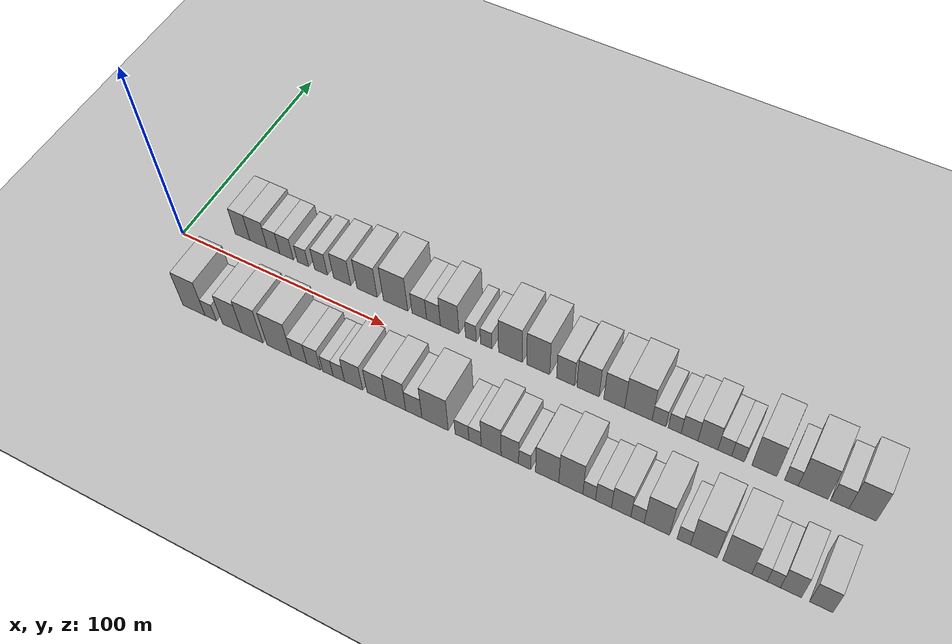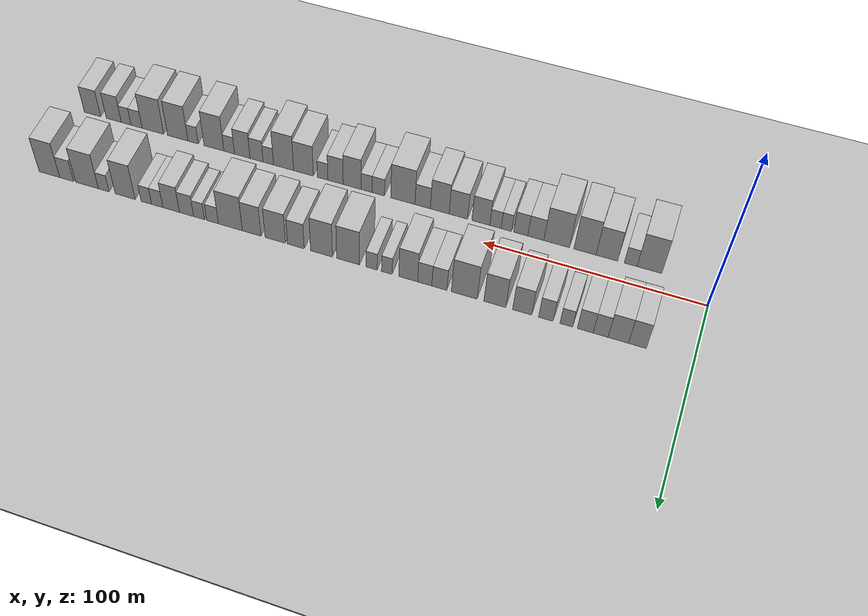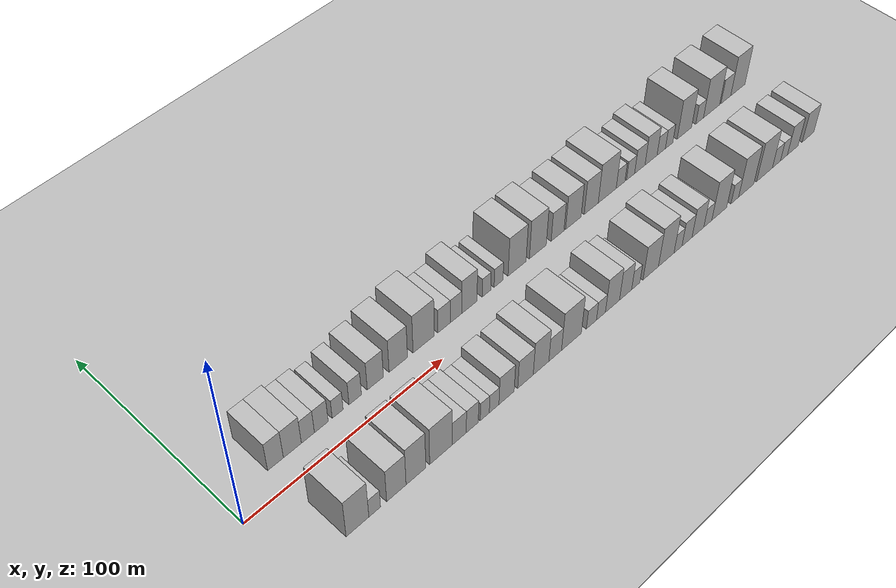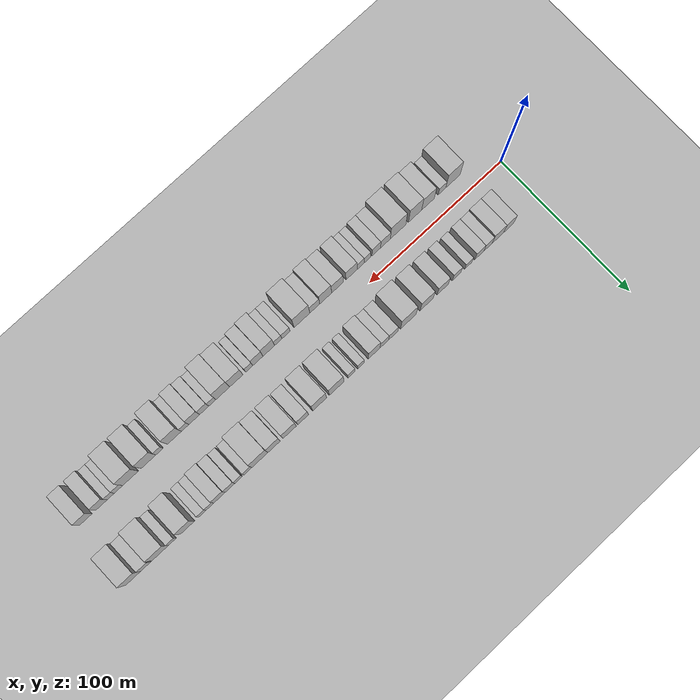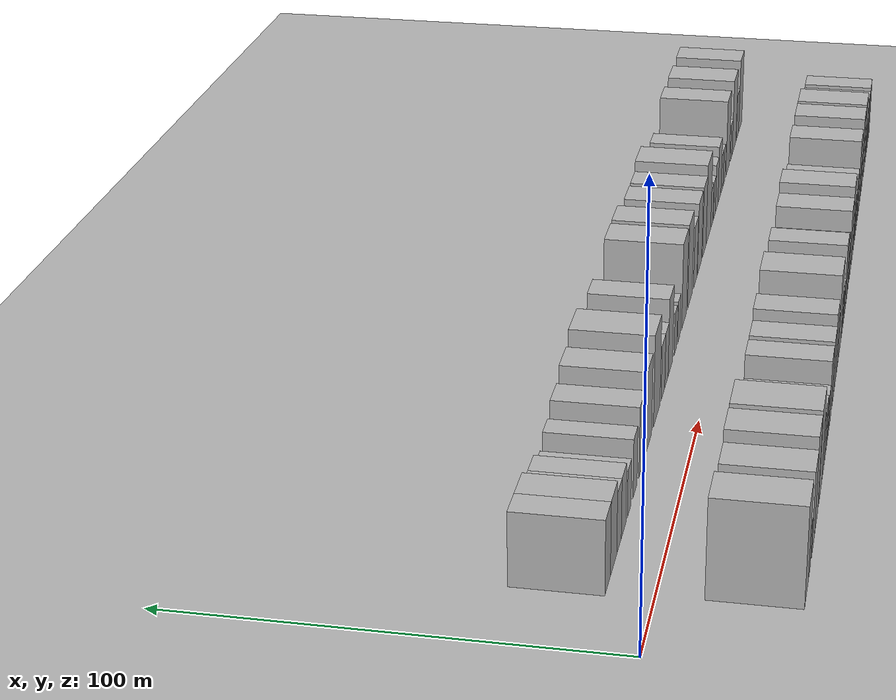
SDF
<?xml version="1.0" encoding="utf-8"?>

<sdf version="1.6">

   <world name="default">

      <gui fullscreen="0">

         <camera name="user_camera">

            <pose>-15 0 4.57585 0 0 0</pose>

            <view_controller>orbit</view_controller>

         </camera>

      </gui>

      <scene>

         <sky>

           <clouds>

             <speed>12</speed>

           </clouds>

         </sky>

         <ambient>0.4 0.4 0.4 1</ambient>

         <background>0.7 0.7 0.7 1</background>

         <shadows>1</shadows>

      </scene>

      <gravity>0 0 -9.8066</gravity>

      <magnetic_field>6e-06 2.3e-05 -4.2e-05</magnetic_field>

      <physics default="0" name="default_physics" type="ode">

         <ode>

            <solver>

               <type>quick</type>

               <iters>10</iters>

               <sor>1.0</sor>

               <use_dynamic_moi_rescaling>0</use_dynamic_moi_rescaling>

            </solver>

            <constraints>

               <cfm>0</cfm>

               <erp>0.2</erp>

               <contact_max_correcting_vel>100</contact_max_correcting_vel>

               <contact_surface_layer>0.001</contact_surface_layer>

            </constraints>

         </ode>

         <max_step_size>0.004</max_step_size>

         <real_time_factor>1</real_time_factor>

         <real_time_update_rate>250</real_time_update_rate>

      </physics>

      <light name="sun" type="directional">

         <cast_shadows>1</cast_shadows>

         <pose>0 0 10 0 0 0</pose>

         <diffuse>0.8 0.8 0.8 1</diffuse>

         <specular>0.2 0.2 0.2 1</specular>

         <attenuation>

            <range>1000</range>

            <constant>0.9</constant>

            <linear>0.01</linear>

            <quadratic>0.001</quadratic>

         </attenuation>

         <direction>-0.5 0.1 -0.9</direction>

      </light>

      <include>

         <name>ground_plane_1</name>

         <uri>model://HANNAS_ground_plane</uri>

         <pose>0 0 0  0 0 0</pose>

      </include>

      <include>

         <name>ground_plane_2</name>

         <uri>model://HANNAS_ground_plane</uri>

         <pose>100 0 0  0 0 0</pose>

      </include>

      <model name="building_1">

         <static>1</static>

         <pose frame="">23.7935 20.0000 0 0.000000 0.000000 1.570796</pose>

         <link name="link">

            <pose frame="">0 0 9.00 0 0 0</pose>

            <collision name="collision">

               <geometry>

                  <box>

                     <size>20.0000 7.5870 18.0000</size>

                  </box>

               </geometry>

               <max_contacts>10</max_contacts>

               <surface>

                  <contact>

                     <ode/>

                  </contact>

                  <bounce/>

                  <friction>

                     <torsional>

                        <ode/>

                     </torsional>

                     <ode/>

                  </friction>

               </surface>

            </collision>

            <visual name="visual">

               <cast_shadows>0</cast_shadows>

               <geometry>

                  <box>

                     <size>20.0000 7.5870 18.0000</size>

                  </box>

               </geometry>

               <material>

                  <script>

                     <uri>model://HANNAS_wall/materials/scripts</uri>

                     <uri>model://HANNAS_wall/materials/textures</uri>

                     <name>vrc/HANNAS_wall</name>

                  </script>

               </material>

            </visual>

            <self_collide>0</self_collide>

            <enable_wind>0</enable_wind>

            <kinematic>0</kinematic>

         </link>

      </model>

      <model name="building_2">

         <static>1</static>

         <pose frame="">31.9652 20.0000 0 0.000000 0.000000 1.570796</pose>

         <link name="link">

            <pose frame="">0 0 9.00 0 0 0</pose>

            <collision name="collision">

               <geometry>

                  <box>

                     <size>20.0000 8.7565 18.0000</size>

                  </box>

               </geometry>

               <max_contacts>10</max_contacts>

               <surface>

                  <contact>

                     <ode/>

                  </contact>

                  <bounce/>

                  <friction>

                     <torsional>

                        <ode/>

                     </torsional>

                     <ode/>

                  </friction>

               </surface>

            </collision>

            <visual name="visual">

               <cast_shadows>0</cast_shadows>

               <geometry>

                  <box>

                     <size>20.0000 8.7565 18.0000</size>

                  </box>

               </geometry>

               <material>

                  <script>

                     <uri>model://HANNAS_wall/materials/scripts</uri>

                     <uri>model://HANNAS_wall/materials/textures</uri>

                     <name>vrc/HANNAS_wall</name>

                  </script>

               </material>

            </visual>

            <self_collide>0</self_collide>

            <enable_wind>0</enable_wind>

            <kinematic>0</kinematic>

         </link>

      </model>

      <model name="building_3">

         <static>1</static>

         <pose frame="">39.5538 20.0000 0 0.000000 0.000000 1.570796</pose>

         <link name="link">

            <pose frame="">0 0 7.50 0 0 0</pose>

            <collision name="collision">

               <geometry>

                  <box>

                     <size>20.0000 6.4206 15.0000</size>

                  </box>

               </geometry>

               <max_contacts>10</max_contacts>

               <surface>

                  <contact>

                     <ode/>

                  </contact>

                  <bounce/>

                  <friction>

                     <torsional>

                        <ode/>

                     </torsional>

                     <ode/>

                  </friction>

               </surface>

            </collision>

            <visual name="visual">

               <cast_shadows>0</cast_shadows>

               <geometry>

                  <box>

                     <size>20.0000 6.4206 15.0000</size>

                  </box>

               </geometry>

               <material>

                  <script>

                     <uri>model://HANNAS_wall/materials/scripts</uri>

                     <uri>model://HANNAS_wall/materials/textures</uri>

                     <name>vrc/HANNAS_wall</name>

                  </script>

               </material>

            </visual>

            <self_collide>0</self_collide>

            <enable_wind>0</enable_wind>

            <kinematic>0</kinematic>

         </link>

      </model>

      <model name="building_4">

         <static>1</static>

         <pose frame="">46.2032 20.0000 0 0.000000 0.000000 1.570796</pose>

         <link name="link">

            <pose frame="">0 0 7.50 0 0 0</pose>

            <collision name="collision">

               <geometry>

                  <box>

                     <size>20.0000 6.8781 15.0000</size>

                  </box>

               </geometry>

               <max_contacts>10</max_contacts>

               <surface>

                  <contact>

                     <ode/>

                  </contact>

                  <bounce/>

                  <friction>

                     <torsional>

                        <ode/>

                     </torsional>

                     <ode/>

                  </friction>

               </surface>

            </collision>

            <visual name="visual">

               <cast_shadows>0</cast_shadows>

               <geometry>

                  <box>

                     <size>20.0000 6.8781 15.0000</size>

                  </box>

               </geometry>

               <material>

                  <script>

                     <uri>model://HANNAS_wall/materials/scripts</uri>

                     <uri>model://HANNAS_wall/materials/textures</uri>

                     <name>vrc/HANNAS_wall</name>

                  </script>

               </material>

            </visual>

            <self_collide>0</self_collide>

            <enable_wind>0</enable_wind>

            <kinematic>0</kinematic>

         </link>

      </model>

      <model name="building_5">

         <static>1</static>

         <pose frame="">54.4073 20.0000 0 0.000000 0.000000 1.570796</pose>

         <link name="link">

            <pose frame="">0 0 6.00 0 0 0</pose>

            <collision name="collision">

               <geometry>

                  <box>

                     <size>20.0000 5.5302 12.0000</size>

                  </box>

               </geometry>

               <max_contacts>10</max_contacts>

               <surface>

                  <contact>

                     <ode/>

                  </contact>

                  <bounce/>

                  <friction>

                     <torsional>

                        <ode/>

                     </torsional>

                     <ode/>

                  </friction>

               </surface>

            </collision>

            <visual name="visual">

               <cast_shadows>0</cast_shadows>

               <geometry>

                  <box>

                     <size>20.0000 5.5302 12.0000</size>

                  </box>

               </geometry>

               <material>

                  <script>

                     <uri>model://HANNAS_wall/materials/scripts</uri>

                     <uri>model://HANNAS_wall/materials/textures</uri>

                     <name>vrc/HANNAS_wall</name>

                  </script>

               </material>

            </visual>

            <self_collide>0</self_collide>

            <enable_wind>0</enable_wind>

            <kinematic>0</kinematic>

         </link>

      </model>

      <model name="building_6">

         <static>1</static>

         <pose frame="">63.3594 20.0000 0 0.000000 0.000000 1.570796</pose>

         <link name="link">

            <pose frame="">0 0 7.50 0 0 0</pose>

            <collision name="collision">

               <geometry>

                  <box>

                     <size>20.0000 6.3739 15.0000</size>

                  </box>

               </geometry>

               <max_contacts>10</max_contacts>

               <surface>

                  <contact>

                     <ode/>

                  </contact>

                  <bounce/>

                  <friction>

                     <torsional>

                        <ode/>

                     </torsional>

                     <ode/>

                  </friction>

               </surface>

            </collision>

            <visual name="visual">

               <cast_shadows>0</cast_shadows>

               <geometry>

                  <box>

                     <size>20.0000 6.3739 15.0000</size>

                  </box>

               </geometry>

               <material>

                  <script>

                     <uri>model://HANNAS_wall/materials/scripts</uri>

                     <uri>model://HANNAS_wall/materials/textures</uri>

                     <name>vrc/HANNAS_wall</name>

                  </script>

               </material>

            </visual>

            <self_collide>0</self_collide>

            <enable_wind>0</enable_wind>

            <kinematic>0</kinematic>

         </link>

      </model>

      <model name="building_7">

         <static>1</static>

         <pose frame="">73.7651 20.0000 0 0.000000 0.000000 1.570796</pose>

         <link name="link">

            <pose frame="">0 0 9.00 0 0 0</pose>

            <collision name="collision">

               <geometry>

                  <box>

                     <size>20.0000 8.4375 18.0000</size>

                  </box>

               </geometry>

               <max_contacts>10</max_contacts>

               <surface>

                  <contact>

                     <ode/>

                  </contact>

                  <bounce/>

                  <friction>

                     <torsional>

                        <ode/>

                     </torsional>

                     <ode/>

                  </friction>

               </surface>

            </collision>

            <visual name="visual">

               <cast_shadows>0</cast_shadows>

               <geometry>

                  <box>

                     <size>20.0000 8.4375 18.0000</size>

                  </box>

               </geometry>

               <material>

                  <script>

                     <uri>model://HANNAS_wall/materials/scripts</uri>

                     <uri>model://HANNAS_wall/materials/textures</uri>

                     <name>vrc/HANNAS_wall</name>

                  </script>

               </material>

            </visual>

            <self_collide>0</self_collide>

            <enable_wind>0</enable_wind>

            <kinematic>0</kinematic>

         </link>

      </model>

      <model name="building_8">

         <static>1</static>

         <pose frame="">85.8713 20.0000 0 0.000000 0.000000 1.570796</pose>

         <link name="link">

            <pose frame="">0 0 10.50 0 0 0</pose>

            <collision name="collision">

               <geometry>

                  <box>

                     <size>20.0000 9.7750 21.0000</size>

                  </box>

               </geometry>

               <max_contacts>10</max_contacts>

               <surface>

                  <contact>

                     <ode/>

                  </contact>

                  <bounce/>

                  <friction>

                     <torsional>

                        <ode/>

                     </torsional>

                     <ode/>

                  </friction>

               </surface>

            </collision>

            <visual name="visual">

               <cast_shadows>0</cast_shadows>

               <geometry>

                  <box>

                     <size>20.0000 9.7750 21.0000</size>

                  </box>

               </geometry>

               <material>

                  <script>

                     <uri>model://HANNAS_wall/materials/scripts</uri>

                     <uri>model://HANNAS_wall/materials/textures</uri>

                     <name>vrc/HANNAS_wall</name>

                  </script>

               </material>

            </visual>

            <self_collide>0</self_collide>

            <enable_wind>0</enable_wind>

            <kinematic>0</kinematic>

         </link>

      </model>

      <model name="building_9">

         <static>1</static>

         <pose frame="">99.5591 20.0000 0 0.000000 0.000000 1.570796</pose>

         <link name="link">

            <pose frame="">0 0 12.00 0 0 0</pose>

            <collision name="collision">

               <geometry>

                  <box>

                     <size>20.0000 11.6007 24.0000</size>

                  </box>

               </geometry>

               <max_contacts>10</max_contacts>

               <surface>

                  <contact>

                     <ode/>

                  </contact>

                  <bounce/>

                  <friction>

                     <torsional>

                        <ode/>

                     </torsional>

                     <ode/>

                  </friction>

               </surface>

            </collision>

            <visual name="visual">

               <cast_shadows>0</cast_shadows>

               <geometry>

                  <box>

                     <size>20.0000 11.6007 24.0000</size>

                  </box>

               </geometry>

               <material>

                  <script>

                     <uri>model://HANNAS_wall/materials/scripts</uri>

                     <uri>model://HANNAS_wall/materials/textures</uri>

                     <name>vrc/HANNAS_wall</name>

                  </script>

               </material>

            </visual>

            <self_collide>0</self_collide>

            <enable_wind>0</enable_wind>

            <kinematic>0</kinematic>

         </link>

      </model>

      <model name="building_10">

         <static>1</static>

         <pose frame="">110.7818 20.0000 0 0.000000 0.000000 1.570796</pose>

         <link name="link">

            <pose frame="">0 0 7.50 0 0 0</pose>

            <collision name="collision">

               <geometry>

                  <box>

                     <size>20.0000 6.8447 15.0000</size>

                  </box>

               </geometry>

               <max_contacts>10</max_contacts>

               <surface>

                  <contact>

                     <ode/>

                  </contact>

                  <bounce/>

                  <friction>

                     <torsional>

                        <ode/>

                     </torsional>

                     <ode/>

                  </friction>

               </surface>

            </collision>

            <visual name="visual">

               <cast_shadows>0</cast_shadows>

               <geometry>

                  <box>

                     <size>20.0000 6.8447 15.0000</size>

                  </box>

               </geometry>

               <material>

                  <script>

                     <uri>model://HANNAS_wall/materials/scripts</uri>

                     <uri>model://HANNAS_wall/materials/textures</uri>

                     <name>vrc/HANNAS_wall</name>

                  </script>

               </material>

            </visual>

            <self_collide>0</self_collide>

            <enable_wind>0</enable_wind>

            <kinematic>0</kinematic>

         </link>

      </model>

      <model name="building_11">

         <static>1</static>

         <pose frame="">117.4213 20.0000 0 0.000000 0.000000 1.570796</pose>

         <link name="link">

            <pose frame="">0 0 7.50 0 0 0</pose>

            <collision name="collision">

               <geometry>

                  <box>

                     <size>20.0000 6.4342 15.0000</size>

                  </box>

               </geometry>

               <max_contacts>10</max_contacts>

               <surface>

                  <contact>

                     <ode/>

                  </contact>

                  <bounce/>

                  <friction>

                     <torsional>

                        <ode/>

                     </torsional>

                     <ode/>

                  </friction>

               </surface>

            </collision>

            <visual name="visual">

               <cast_shadows>0</cast_shadows>

               <geometry>

                  <box>

                     <size>20.0000 6.4342 15.0000</size>

                  </box>

               </geometry>

               <material>

                  <script>

                     <uri>model://HANNAS_wall/materials/scripts</uri>

                     <uri>model://HANNAS_wall/materials/textures</uri>

                     <name>vrc/HANNAS_wall</name>

                  </script>

               </material>

            </visual>

            <self_collide>0</self_collide>

            <enable_wind>0</enable_wind>

            <kinematic>0</kinematic>

         </link>

      </model>

      <model name="building_12">

         <static>1</static>

         <pose frame="">124.9499 20.0000 0 0.000000 0.000000 1.570796</pose>

         <link name="link">

            <pose frame="">0 0 10.50 0 0 0</pose>

            <collision name="collision">

               <geometry>

                  <box>

                     <size>20.0000 8.6229 21.0000</size>

                  </box>

               </geometry>

               <max_contacts>10</max_contacts>

               <surface>

                  <contact>

                     <ode/>

                  </contact>

                  <bounce/>

                  <friction>

                     <torsional>

                        <ode/>

                     </torsional>

                     <ode/>

                  </friction>

               </surface>

            </collision>

            <visual name="visual">

               <cast_shadows>0</cast_shadows>

               <geometry>

                  <box>

                     <size>20.0000 8.6229 21.0000</size>

                  </box>

               </geometry>

               <material>

                  <script>

                     <uri>model://HANNAS_wall/materials/scripts</uri>

                     <uri>model://HANNAS_wall/materials/textures</uri>

                     <name>vrc/HANNAS_wall</name>

                  </script>

               </material>

            </visual>

            <self_collide>0</self_collide>

            <enable_wind>0</enable_wind>

            <kinematic>0</kinematic>

         </link>

      </model>

      <model name="building_13">

         <static>1</static>

         <pose frame="">134.7088 20.0000 0 0.000000 0.000000 1.570796</pose>

         <link name="link">

            <pose frame="">0 0 6.00 0 0 0</pose>

            <collision name="collision">

               <geometry>

                  <box>

                     <size>20.0000 4.8948 12.0000</size>

                  </box>

               </geometry>

               <max_contacts>10</max_contacts>

               <surface>

                  <contact>

                     <ode/>

                  </contact>

                  <bounce/>

                  <friction>

                     <torsional>

                        <ode/>

                     </torsional>

                     <ode/>

                  </friction>

               </surface>

            </collision>

            <visual name="visual">

               <cast_shadows>0</cast_shadows>

               <geometry>

                  <box>

                     <size>20.0000 4.8948 12.0000</size>

                  </box>

               </geometry>

               <material>

                  <script>

                     <uri>model://HANNAS_wall/materials/scripts</uri>

                     <uri>model://HANNAS_wall/materials/textures</uri>

                     <name>vrc/HANNAS_wall</name>

                  </script>

               </material>

            </visual>

            <self_collide>0</self_collide>

            <enable_wind>0</enable_wind>

            <kinematic>0</kinematic>

         </link>

      </model>

      <model name="building_14">

         <static>1</static>

         <pose frame="">141.7410 20.0000 0 0.000000 0.000000 1.570796</pose>

         <link name="link">

            <pose frame="">0 0 6.00 0 0 0</pose>

            <collision name="collision">

               <geometry>

                  <box>

                     <size>20.0000 5.1697 12.0000</size>

                  </box>

               </geometry>

               <max_contacts>10</max_contacts>

               <surface>

                  <contact>

                     <ode/>

                  </contact>

                  <bounce/>

                  <friction>

                     <torsional>

                        <ode/>

                     </torsional>

                     <ode/>

                  </friction>

               </surface>

            </collision>

            <visual name="visual">

               <cast_shadows>0</cast_shadows>

               <geometry>

                  <box>

                     <size>20.0000 5.1697 12.0000</size>

                  </box>

               </geometry>

               <material>

                  <script>

                     <uri>model://HANNAS_wall/materials/scripts</uri>

                     <uri>model://HANNAS_wall/materials/textures</uri>

                     <name>vrc/HANNAS_wall</name>

                  </script>

               </material>

            </visual>

            <self_collide>0</self_collide>

            <enable_wind>0</enable_wind>

            <kinematic>0</kinematic>

         </link>

      </model>

      <model name="building_15">

         <static>1</static>

         <pose frame="">152.6574 20.0000 0 0.000000 0.000000 1.570796</pose>

         <link name="link">

            <pose frame="">0 0 12.00 0 0 0</pose>

            <collision name="collision">

               <geometry>

                  <box>

                     <size>20.0000 10.6631 24.0000</size>

                  </box>

               </geometry>

               <max_contacts>10</max_contacts>

               <surface>

                  <contact>

                     <ode/>

                  </contact>

                  <bounce/>

                  <friction>

                     <torsional>

                        <ode/>

                     </torsional>

                     <ode/>

                  </friction>

               </surface>

            </collision>

            <visual name="visual">

               <cast_shadows>0</cast_shadows>

               <geometry>

                  <box>

                     <size>20.0000 10.6631 24.0000</size>

                  </box>

               </geometry>

               <material>

                  <script>

                     <uri>model://HANNAS_wall/materials/scripts</uri>

                     <uri>model://HANNAS_wall/materials/textures</uri>

                     <name>vrc/HANNAS_wall</name>

                  </script>

               </material>

            </visual>

            <self_collide>0</self_collide>

            <enable_wind>0</enable_wind>

            <kinematic>0</kinematic>

         </link>

      </model>

      <model name="building_16">

         <static>1</static>

         <pose frame="">165.0884 20.0000 0 0.000000 0.000000 1.570796</pose>

         <link name="link">

            <pose frame="">0 0 12.00 0 0 0</pose>

            <collision name="collision">

               <geometry>

                  <box>

                     <size>20.0000 10.1989 24.0000</size>

                  </box>

               </geometry>

               <max_contacts>10</max_contacts>

               <surface>

                  <contact>

                     <ode/>

                  </contact>

                  <bounce/>

                  <friction>

                     <torsional>

                        <ode/>

                     </torsional>

                     <ode/>

                  </friction>

               </surface>

            </collision>

            <visual name="visual">

               <cast_shadows>0</cast_shadows>

               <geometry>

                  <box>

                     <size>20.0000 10.1989 24.0000</size>

                  </box>

               </geometry>

               <material>

                  <script>

                     <uri>model://HANNAS_wall/materials/scripts</uri>

                     <uri>model://HANNAS_wall/materials/textures</uri>

                     <name>vrc/HANNAS_wall</name>

                  </script>

               </material>

            </visual>

            <self_collide>0</self_collide>

            <enable_wind>0</enable_wind>

            <kinematic>0</kinematic>

         </link>

      </model>

      <model name="building_17">

         <static>1</static>

         <pose frame="">177.1372 20.0000 0 0.000000 0.000000 1.570796</pose>

         <link name="link">

            <pose frame="">0 0 9.00 0 0 0</pose>

            <collision name="collision">

               <geometry>

                  <box>

                     <size>20.0000 7.8987 18.0000</size>

                  </box>

               </geometry>

               <max_contacts>10</max_contacts>

               <surface>

                  <contact>

                     <ode/>

                  </contact>

                  <bounce/>

                  <friction>

                     <torsional>

                        <ode/>

                     </torsional>

                     <ode/>

                  </friction>

               </surface>

            </collision>

            <visual name="visual">

               <cast_shadows>0</cast_shadows>

               <geometry>

                  <box>

                     <size>20.0000 7.8987 18.0000</size>

                  </box>

               </geometry>

               <material>

                  <script>

                     <uri>model://HANNAS_wall/materials/scripts</uri>

                     <uri>model://HANNAS_wall/materials/textures</uri>

                     <name>vrc/HANNAS_wall</name>

                  </script>

               </material>

            </visual>

            <self_collide>0</self_collide>

            <enable_wind>0</enable_wind>

            <kinematic>0</kinematic>

         </link>

      </model>

      <model name="building_18">

         <static>1</static>

         <pose frame="">186.9221 20.0000 0 0.000000 0.000000 1.570796</pose>

         <link name="link">

            <pose frame="">0 0 10.50 0 0 0</pose>

            <collision name="collision">

               <geometry>

                  <box>

                     <size>20.0000 9.6711 21.0000</size>

                  </box>

               </geometry>

               <max_contacts>10</max_contacts>

               <surface>

                  <contact>

                     <ode/>

                  </contact>

                  <bounce/>

                  <friction>

                     <torsional>

                        <ode/>

                     </torsional>

                     <ode/>

                  </friction>

               </surface>

            </collision>

            <visual name="visual">

               <cast_shadows>0</cast_shadows>

               <geometry>

                  <box>

                     <size>20.0000 9.6711 21.0000</size>

                  </box>

               </geometry>

               <material>

                  <script>

                     <uri>model://HANNAS_wall/materials/scripts</uri>

                     <uri>model://HANNAS_wall/materials/textures</uri>

                     <name>vrc/HANNAS_wall</name>

                  </script>

               </material>

            </visual>

            <self_collide>0</self_collide>

            <enable_wind>0</enable_wind>

            <kinematic>0</kinematic>

         </link>

      </model>

      <model name="building_19">

         <static>1</static>

         <pose frame="">198.2208 20.0000 0 0.000000 0.000000 1.570796</pose>

         <link name="link">

            <pose frame="">0 0 10.50 0 0 0</pose>

            <collision name="collision">

               <geometry>

                  <box>

                     <size>20.0000 8.9264 21.0000</size>

                  </box>

               </geometry>

               <max_contacts>10</max_contacts>

               <surface>

                  <contact>

                     <ode/>

                  </contact>

                  <bounce/>

                  <friction>

                     <torsional>

                        <ode/>

                     </torsional>

                     <ode/>

                  </friction>

               </surface>

            </collision>

            <visual name="visual">

               <cast_shadows>0</cast_shadows>

               <geometry>

                  <box>

                     <size>20.0000 8.9264 21.0000</size>

                  </box>

               </geometry>

               <material>

                  <script>

                     <uri>model://HANNAS_wall/materials/scripts</uri>

                     <uri>model://HANNAS_wall/materials/textures</uri>

                     <name>vrc/HANNAS_wall</name>

                  </script>

               </material>

            </visual>

            <self_collide>0</self_collide>

            <enable_wind>0</enable_wind>

            <kinematic>0</kinematic>

         </link>

      </model>

      <model name="building_20">

         <static>1</static>

         <pose frame="">208.4847 20.0000 0 0.000000 0.000000 1.570796</pose>

         <link name="link">

            <pose frame="">0 0 12.00 0 0 0</pose>

            <collision name="collision">

               <geometry>

                  <box>

                     <size>20.0000 11.6013 24.0000</size>

                  </box>

               </geometry>

               <max_contacts>10</max_contacts>

               <surface>

                  <contact>

                     <ode/>

                  </contact>

                  <bounce/>

                  <friction>

                     <torsional>

                        <ode/>

                     </torsional>

                     <ode/>

                  </friction>

               </surface>

            </collision>

            <visual name="visual">

               <cast_shadows>0</cast_shadows>

               <geometry>

                  <box>

                     <size>20.0000 11.6013 24.0000</size>

                  </box>

               </geometry>

               <material>

                  <script>

                     <uri>model://HANNAS_wall/materials/scripts</uri>

                     <uri>model://HANNAS_wall/materials/textures</uri>

                     <name>vrc/HANNAS_wall</name>

                  </script>

               </material>

            </visual>

            <self_collide>0</self_collide>

            <enable_wind>0</enable_wind>

            <kinematic>0</kinematic>

         </link>

      </model>

      <model name="building_21">

         <static>1</static>

         <pose frame="">217.1560 20.0000 0 0.000000 0.000000 1.570796</pose>

         <link name="link">

            <pose frame="">0 0 6.00 0 0 0</pose>

            <collision name="collision">

               <geometry>

                  <box>

                     <size>20.0000 5.7415 12.0000</size>

                  </box>

               </geometry>

               <max_contacts>10</max_contacts>

               <surface>

                  <contact>

                     <ode/>

                  </contact>

                  <bounce/>

                  <friction>

                     <torsional>

                        <ode/>

                     </torsional>

                     <ode/>

                  </friction>

               </surface>

            </collision>

            <visual name="visual">

               <cast_shadows>0</cast_shadows>

               <geometry>

                  <box>

                     <size>20.0000 5.7415 12.0000</size>

                  </box>

               </geometry>

               <material>

                  <script>

                     <uri>model://HANNAS_wall/materials/scripts</uri>

                     <uri>model://HANNAS_wall/materials/textures</uri>

                     <name>vrc/HANNAS_wall</name>

                  </script>

               </material>

            </visual>

            <self_collide>0</self_collide>

            <enable_wind>0</enable_wind>

            <kinematic>0</kinematic>

         </link>

      </model>

      <model name="building_22">

         <static>1</static>

         <pose frame="">223.7144 20.0000 0 0.000000 0.000000 1.570796</pose>

         <link name="link">

            <pose frame="">0 0 6.00 0 0 0</pose>

            <collision name="collision">

               <geometry>

                  <box>

                     <size>20.0000 5.3753 12.0000</size>

                  </box>

               </geometry>

               <max_contacts>10</max_contacts>

               <surface>

                  <contact>

                     <ode/>

                  </contact>

                  <bounce/>

                  <friction>

                     <torsional>

                        <ode/>

                     </torsional>

                     <ode/>

                  </friction>

               </surface>

            </collision>

            <visual name="visual">

               <cast_shadows>0</cast_shadows>

               <geometry>

                  <box>

                     <size>20.0000 5.3753 12.0000</size>

                  </box>

               </geometry>

               <material>

                  <script>

                     <uri>model://HANNAS_wall/materials/scripts</uri>

                     <uri>model://HANNAS_wall/materials/textures</uri>

                     <name>vrc/HANNAS_wall</name>

                  </script>

               </material>

            </visual>

            <self_collide>0</self_collide>

            <enable_wind>0</enable_wind>

            <kinematic>0</kinematic>

         </link>

      </model>

      <model name="building_23">

         <static>1</static>

         <pose frame="">229.8600 20.0000 0 0.000000 0.000000 1.570796</pose>

         <link name="link">

            <pose frame="">0 0 7.50 0 0 0</pose>

            <collision name="collision">

               <geometry>

                  <box>

                     <size>20.0000 6.9158 15.0000</size>

                  </box>

               </geometry>

               <max_contacts>10</max_contacts>

               <surface>

                  <contact>

                     <ode/>

                  </contact>

                  <bounce/>

                  <friction>

                     <torsional>

                        <ode/>

                     </torsional>

                     <ode/>

                  </friction>

               </surface>

            </collision>

            <visual name="visual">

               <cast_shadows>0</cast_shadows>

               <geometry>

                  <box>

                     <size>20.0000 6.9158 15.0000</size>

                  </box>

               </geometry>

               <material>

                  <script>

                     <uri>model://HANNAS_wall/materials/scripts</uri>

                     <uri>model://HANNAS_wall/materials/textures</uri>

                     <name>vrc/HANNAS_wall</name>

                  </script>

               </material>

            </visual>

            <self_collide>0</self_collide>

            <enable_wind>0</enable_wind>

            <kinematic>0</kinematic>

         </link>

      </model>

      <model name="building_24">

         <static>1</static>

         <pose frame="">237.3918 20.0000 0 0.000000 0.000000 1.570796</pose>

         <link name="link">

            <pose frame="">0 0 9.00 0 0 0</pose>

            <collision name="collision">

               <geometry>

                  <box>

                     <size>20.0000 8.1478 18.0000</size>

                  </box>

               </geometry>

               <max_contacts>10</max_contacts>

               <surface>

                  <contact>

                     <ode/>

                  </contact>

                  <bounce/>

                  <friction>

                     <torsional>

                        <ode/>

                     </torsional>

                     <ode/>

                  </friction>

               </surface>

            </collision>

            <visual name="visual">

               <cast_shadows>0</cast_shadows>

               <geometry>

                  <box>

                     <size>20.0000 8.1478 18.0000</size>

                  </box>

               </geometry>

               <material>

                  <script>

                     <uri>model://HANNAS_wall/materials/scripts</uri>

                     <uri>model://HANNAS_wall/materials/textures</uri>

                     <name>vrc/HANNAS_wall</name>

                  </script>

               </material>

            </visual>

            <self_collide>0</self_collide>

            <enable_wind>0</enable_wind>

            <kinematic>0</kinematic>

         </link>

      </model>

      <model name="building_25">

         <static>1</static>

         <pose frame="">244.2864 20.0000 0 0.000000 0.000000 1.570796</pose>

         <link name="link">

            <pose frame="">0 0 6.00 0 0 0</pose>

            <collision name="collision">

               <geometry>

                  <box>

                     <size>20.0000 5.6413 12.0000</size>

                  </box>

               </geometry>

               <max_contacts>10</max_contacts>

               <surface>

                  <contact>

                     <ode/>

                  </contact>

                  <bounce/>

                  <friction>

                     <torsional>

                        <ode/>

                     </torsional>

                     <ode/>

                  </friction>

               </surface>

            </collision>

            <visual name="visual">

               <cast_shadows>0</cast_shadows>

               <geometry>

                  <box>

                     <size>20.0000 5.6413 12.0000</size>

                  </box>

               </geometry>

               <material>

                  <script>

                     <uri>model://HANNAS_wall/materials/scripts</uri>

                     <uri>model://HANNAS_wall/materials/textures</uri>

                     <name>vrc/HANNAS_wall</name>

                  </script>

               </material>

            </visual>

            <self_collide>0</self_collide>

            <enable_wind>0</enable_wind>

            <kinematic>0</kinematic>

         </link>

      </model>

      <model name="building_26">

         <static>1</static>

         <pose frame="">249.6790 20.0000 0 0.000000 0.000000 1.570796</pose>

         <link name="link">

            <pose frame="">0 0 6.00 0 0 0</pose>

            <collision name="collision">

               <geometry>

                  <box>

                     <size>20.0000 5.1438 12.0000</size>

                  </box>

               </geometry>

               <max_contacts>10</max_contacts>

               <surface>

                  <contact>

                     <ode/>

                  </contact>

                  <bounce/>

                  <friction>

                     <torsional>

                        <ode/>

                     </torsional>

                     <ode/>

                  </friction>

               </surface>

            </collision>

            <visual name="visual">

               <cast_shadows>0</cast_shadows>

               <geometry>

                  <box>

                     <size>20.0000 5.1438 12.0000</size>

                  </box>

               </geometry>

               <material>

                  <script>

                     <uri>model://HANNAS_wall/materials/scripts</uri>

                     <uri>model://HANNAS_wall/materials/textures</uri>

                     <name>vrc/HANNAS_wall</name>

                  </script>

               </material>

            </visual>

            <self_collide>0</self_collide>

            <enable_wind>0</enable_wind>

            <kinematic>0</kinematic>

         </link>

      </model>

      <model name="building_27">

         <static>1</static>

         <pose frame="">260.2648 20.0000 0 0.000000 0.000000 1.570796</pose>

         <link name="link">

            <pose frame="">0 0 12.00 0 0 0</pose>

            <collision name="collision">

               <geometry>

                  <box>

                     <size>20.0000 10.0279 24.0000</size>

                  </box>

               </geometry>

               <max_contacts>10</max_contacts>

               <surface>

                  <contact>

                     <ode/>

                  </contact>

                  <bounce/>

                  <friction>

                     <torsional>

                        <ode/>

                     </torsional>

                     <ode/>

                  </friction>

               </surface>

            </collision>

            <visual name="visual">

               <cast_shadows>0</cast_shadows>

               <geometry>

                  <box>

                     <size>20.0000 10.0279 24.0000</size>

                  </box>

               </geometry>

               <material>

                  <script>

                     <uri>model://HANNAS_wall/materials/scripts</uri>

                     <uri>model://HANNAS_wall/materials/textures</uri>

                     <name>vrc/HANNAS_wall</name>

                  </script>

               </material>

            </visual>

            <self_collide>0</self_collide>

            <enable_wind>0</enable_wind>

            <kinematic>0</kinematic>

         </link>

      </model>

      <model name="building_28">

         <static>1</static>

         <pose frame="">270.9927 20.0000 0 0.000000 0.000000 1.570796</pose>

         <link name="link">

            <pose frame="">0 0 6.00 0 0 0</pose>

            <collision name="collision">

               <geometry>

                  <box>

                     <size>20.0000 5.4278 12.0000</size>

                  </box>

               </geometry>

               <max_contacts>10</max_contacts>

               <surface>

                  <contact>

                     <ode/>

                  </contact>

                  <bounce/>

                  <friction>

                     <torsional>

                        <ode/>

                     </torsional>

                     <ode/>

                  </friction>

               </surface>

            </collision>

            <visual name="visual">

               <cast_shadows>0</cast_shadows>

               <geometry>

                  <box>

                     <size>20.0000 5.4278 12.0000</size>

                  </box>

               </geometry>

               <material>

                  <script>

                     <uri>model://HANNAS_wall/materials/scripts</uri>

                     <uri>model://HANNAS_wall/materials/textures</uri>

                     <name>vrc/HANNAS_wall</name>

                  </script>

               </material>

            </visual>

            <self_collide>0</self_collide>

            <enable_wind>0</enable_wind>

            <kinematic>0</kinematic>

         </link>

      </model>

      <model name="building_29">

         <static>1</static>

         <pose frame="">279.4799 20.0000 0 0.000000 0.000000 1.570796</pose>

         <link name="link">

            <pose frame="">0 0 12.00 0 0 0</pose>

            <collision name="collision">

               <geometry>

                  <box>

                     <size>20.0000 11.5467 24.0000</size>

                  </box>

               </geometry>

               <max_contacts>10</max_contacts>

               <surface>

                  <contact>

                     <ode/>

                  </contact>

                  <bounce/>

                  <friction>

                     <torsional>

                        <ode/>

                     </torsional>

                     <ode/>

                  </friction>

               </surface>

            </collision>

            <visual name="visual">

               <cast_shadows>0</cast_shadows>

               <geometry>

                  <box>

                     <size>20.0000 11.5467 24.0000</size>

                  </box>

               </geometry>

               <material>

                  <script>

                     <uri>model://HANNAS_wall/materials/scripts</uri>

                     <uri>model://HANNAS_wall/materials/textures</uri>

                     <name>vrc/HANNAS_wall</name>

                  </script>

               </material>

            </visual>

            <self_collide>0</self_collide>

            <enable_wind>0</enable_wind>

            <kinematic>0</kinematic>

         </link>

      </model>

      <model name="building_30">

         <static>1</static>

         <pose frame="">289.8093 20.0000 0 0.000000 0.000000 1.570796</pose>

         <link name="link">

            <pose frame="">0 0 7.50 0 0 0</pose>

            <collision name="collision">

               <geometry>

                  <box>

                     <size>20.0000 7.1120 15.0000</size>

                  </box>

               </geometry>

               <max_contacts>10</max_contacts>

               <surface>

                  <contact>

                     <ode/>

                  </contact>

                  <bounce/>

                  <friction>

                     <torsional>

                        <ode/>

                     </torsional>

                     <ode/>

                  </friction>

               </surface>

            </collision>

            <visual name="visual">

               <cast_shadows>0</cast_shadows>

               <geometry>

                  <box>

                     <size>20.0000 7.1120 15.0000</size>

                  </box>

               </geometry>

               <material>

                  <script>

                     <uri>model://HANNAS_wall/materials/scripts</uri>

                     <uri>model://HANNAS_wall/materials/textures</uri>

                     <name>vrc/HANNAS_wall</name>

                  </script>

               </material>

            </visual>

            <self_collide>0</self_collide>

            <enable_wind>0</enable_wind>

            <kinematic>0</kinematic>

         </link>

      </model>

      <model name="building_31">

         <static>1</static>

         <pose frame="">298.6134 20.0000 0 0.000000 0.000000 1.570796</pose>

         <link name="link">

            <pose frame="">0 0 12.00 0 0 0</pose>

            <collision name="collision">

               <geometry>

                  <box>

                     <size>20.0000 10.4963 24.0000</size>

                  </box>

               </geometry>

               <max_contacts>10</max_contacts>

               <surface>

                  <contact>

                     <ode/>

                  </contact>

                  <bounce/>

                  <friction>

                     <torsional>

                        <ode/>

                     </torsional>

                     <ode/>

                  </friction>

               </surface>

            </collision>

            <visual name="visual">

               <cast_shadows>0</cast_shadows>

               <geometry>

                  <box>

                     <size>20.0000 10.4963 24.0000</size>

                  </box>

               </geometry>

               <material>

                  <script>

                     <uri>model://HANNAS_wall/materials/scripts</uri>

                     <uri>model://HANNAS_wall/materials/textures</uri>

                     <name>vrc/HANNAS_wall</name>

                  </script>

               </material>

            </visual>

            <self_collide>0</self_collide>

            <enable_wind>0</enable_wind>

            <kinematic>0</kinematic>

         </link>

      </model>

      <model name="building_32">

         <static>1</static>

         <pose frame="">27.4905 -20.0000 0 0.000000 0.000000 1.570796</pose>

         <link name="link">

            <pose frame="">0 0 12.00 0 0 0</pose>

            <collision name="collision">

               <geometry>

                  <box>

                     <size>20.0000 10.9810 24.0000</size>

                  </box>

               </geometry>

               <max_contacts>10</max_contacts>

               <surface>

                  <contact>

                     <ode/>

                  </contact>

                  <bounce/>

                  <friction>

                     <torsional>

                        <ode/>

                     </torsional>

                     <ode/>

                  </friction>

               </surface>

            </collision>

            <visual name="visual">

               <cast_shadows>0</cast_shadows>

               <geometry>

                  <box>

                     <size>20.0000 10.9810 24.0000</size>

                  </box>

               </geometry>

               <material>

                  <script>

                     <uri>model://HANNAS_wall/materials/scripts</uri>

                     <uri>model://HANNAS_wall/materials/textures</uri>

                     <name>vrc/HANNAS_wall</name>

                  </script>

               </material>

            </visual>

            <self_collide>0</self_collide>

            <enable_wind>0</enable_wind>

            <kinematic>0</kinematic>

         </link>

      </model>

      <model name="building_33">

         <static>1</static>

         <pose frame="">35.8267 -20.0000 0 0.000000 0.000000 1.570796</pose>

         <link name="link">

            <pose frame="">0 0 6.00 0 0 0</pose>

            <collision name="collision">

               <geometry>

                  <box>

                     <size>20.0000 5.6913 12.0000</size>

                  </box>

               </geometry>

               <max_contacts>10</max_contacts>

               <surface>

                  <contact>

                     <ode/>

                  </contact>

                  <bounce/>

                  <friction>

                     <torsional>

                        <ode/>

                     </torsional>

                     <ode/>

                  </friction>

               </surface>

            </collision>

            <visual name="visual">

               <cast_shadows>0</cast_shadows>

               <geometry>

                  <box>

                     <size>20.0000 5.6913 12.0000</size>

                  </box>

               </geometry>

               <material>

                  <script>

                     <uri>model://HANNAS_wall/materials/scripts</uri>

                     <uri>model://HANNAS_wall/materials/textures</uri>

                     <name>vrc/HANNAS_wall</name>

                  </script>

               </material>

            </visual>

            <self_collide>0</self_collide>

            <enable_wind>0</enable_wind>

            <kinematic>0</kinematic>

         </link>

      </model>

      <model name="building_34">

         <static>1</static>

         <pose frame="">46.5009 -20.0000 0 0.000000 0.000000 1.570796</pose>

         <link name="link">

            <pose frame="">0 0 10.50 0 0 0</pose>

            <collision name="collision">

               <geometry>

                  <box>

                     <size>20.0000 9.6571 21.0000</size>

                  </box>

               </geometry>

               <max_contacts>10</max_contacts>

               <surface>

                  <contact>

                     <ode/>

                  </contact>

                  <bounce/>

                  <friction>

                     <torsional>

                        <ode/>

                     </torsional>

                     <ode/>

                  </friction>

               </surface>

            </collision>

            <visual name="visual">

               <cast_shadows>0</cast_shadows>

               <geometry>

                  <box>

                     <size>20.0000 9.6571 21.0000</size>

                  </box>

               </geometry>

               <material>

                  <script>

                     <uri>model://HANNAS_wall/materials/scripts</uri>

                     <uri>model://HANNAS_wall/materials/textures</uri>

                     <name>vrc/HANNAS_wall</name>

                  </script>

               </material>

            </visual>

            <self_collide>0</self_collide>

            <enable_wind>0</enable_wind>

            <kinematic>0</kinematic>

         </link>

      </model>

      <model name="building_35">

         <static>1</static>

         <pose frame="">56.3222 -20.0000 0 0.000000 0.000000 1.570796</pose>

         <link name="link">

            <pose frame="">0 0 12.00 0 0 0</pose>

            <collision name="collision">

               <geometry>

                  <box>

                     <size>20.0000 9.9856 24.0000</size>

                  </box>

               </geometry>

               <max_contacts>10</max_contacts>

               <surface>

                  <contact>

                     <ode/>

                  </contact>

                  <bounce/>

                  <friction>

                     <torsional>

                        <ode/>

                     </torsional>

                     <ode/>

                  </friction>

               </surface>

            </collision>

            <visual name="visual">

               <cast_shadows>0</cast_shadows>

               <geometry>

                  <box>

                     <size>20.0000 9.9856 24.0000</size>

                  </box>

               </geometry>

               <material>

                  <script>

                     <uri>model://HANNAS_wall/materials/scripts</uri>

                     <uri>model://HANNAS_wall/materials/textures</uri>

                     <name>vrc/HANNAS_wall</name>

                  </script>

               </material>

            </visual>

            <self_collide>0</self_collide>

            <enable_wind>0</enable_wind>

            <kinematic>0</kinematic>

         </link>

      </model>

      <model name="building_36">

         <static>1</static>

         <pose frame="">69.1552 -20.0000 0 0.000000 0.000000 1.570796</pose>

         <link name="link">

            <pose frame="">0 0 12.00 0 0 0</pose>

            <collision name="collision">

               <geometry>

                  <box>

                     <size>20.0000 11.6805 24.0000</size>

                  </box>

               </geometry>

               <max_contacts>10</max_contacts>

               <surface>

                  <contact>

                     <ode/>

                  </contact>

                  <bounce/>

                  <friction>

                     <torsional>

                        <ode/>

                     </torsional>

                     <ode/>

                  </friction>

               </surface>

            </collision>

            <visual name="visual">

               <cast_shadows>0</cast_shadows>

               <geometry>

                  <box>

                     <size>20.0000 11.6805 24.0000</size>

                  </box>

               </geometry>

               <material>

                  <script>

                     <uri>model://HANNAS_wall/materials/scripts</uri>

                     <uri>model://HANNAS_wall/materials/textures</uri>

                     <name>vrc/HANNAS_wall</name>

                  </script>

               </material>

            </visual>

            <self_collide>0</self_collide>

            <enable_wind>0</enable_wind>

            <kinematic>0</kinematic>

         </link>

      </model>

      <model name="building_37">

         <static>1</static>

         <pose frame="">78.6753 -20.0000 0 0.000000 0.000000 1.570796</pose>

         <link name="link">

            <pose frame="">0 0 7.50 0 0 0</pose>

            <collision name="collision">

               <geometry>

                  <box>

                     <size>20.0000 7.3597 15.0000</size>

                  </box>

               </geometry>

               <max_contacts>10</max_contacts>

               <surface>

                  <contact>

                     <ode/>

                  </contact>

                  <bounce/>

                  <friction>

                     <torsional>

                        <ode/>

                     </torsional>

                     <ode/>

                  </friction>

               </surface>

            </collision>

            <visual name="visual">

               <cast_shadows>0</cast_shadows>

               <geometry>

                  <box>

                     <size>20.0000 7.3597 15.0000</size>

                  </box>

               </geometry>

               <material>

                  <script>

                     <uri>model://HANNAS_wall/materials/scripts</uri>

                     <uri>model://HANNAS_wall/materials/textures</uri>

                     <name>vrc/HANNAS_wall</name>

                  </script>

               </material>

            </visual>

            <self_collide>0</self_collide>

            <enable_wind>0</enable_wind>

            <kinematic>0</kinematic>

         </link>

      </model>

      <model name="building_38">

         <static>1</static>

         <pose frame="">85.5748 -20.0000 0 0.000000 0.000000 1.570796</pose>

         <link name="link">

            <pose frame="">0 0 7.50 0 0 0</pose>

            <collision name="collision">

               <geometry>

                  <box>

                     <size>20.0000 6.4391 15.0000</size>

                  </box>

               </geometry>

               <max_contacts>10</max_contacts>

               <surface>

                  <contact>

                     <ode/>

                  </contact>

                  <bounce/>

                  <friction>

                     <torsional>

                        <ode/>

                     </torsional>

                     <ode/>

                  </friction>

               </surface>

            </collision>

            <visual name="visual">

               <cast_shadows>0</cast_shadows>

               <geometry>

                  <box>

                     <size>20.0000 6.4391 15.0000</size>

                  </box>

               </geometry>

               <material>

                  <script>

                     <uri>model://HANNAS_wall/materials/scripts</uri>

                     <uri>model://HANNAS_wall/materials/textures</uri>

                     <name>vrc/HANNAS_wall</name>

                  </script>

               </material>

            </visual>

            <self_collide>0</self_collide>

            <enable_wind>0</enable_wind>

            <kinematic>0</kinematic>

         </link>

      </model>

      <model name="building_39">

         <static>1</static>

         <pose frame="">92.2370 -20.0000 0 0.000000 0.000000 1.570796</pose>

         <link name="link">

            <pose frame="">0 0 6.00 0 0 0</pose>

            <collision name="collision">

               <geometry>

                  <box>

                     <size>20.0000 4.8854 12.0000</size>

                  </box>

               </geometry>

               <max_contacts>10</max_contacts>

               <surface>

                  <contact>

                     <ode/>

                  </contact>

                  <bounce/>

                  <friction>

                     <torsional>

                        <ode/>

                     </torsional>

                     <ode/>

                  </friction>

               </surface>

            </collision>

            <visual name="visual">

               <cast_shadows>0</cast_shadows>

               <geometry>

                  <box>

                     <size>20.0000 4.8854 12.0000</size>

                  </box>

               </geometry>

               <material>

                  <script>

                     <uri>model://HANNAS_wall/materials/scripts</uri>

                     <uri>model://HANNAS_wall/materials/textures</uri>

                     <name>vrc/HANNAS_wall</name>

                  </script>

               </material>

            </visual>

            <self_collide>0</self_collide>

            <enable_wind>0</enable_wind>

            <kinematic>0</kinematic>

         </link>

      </model>

      <model name="building_40">

         <static>1</static>

         <pose frame="">97.3069 -20.0000 0 0.000000 0.000000 1.570796</pose>

         <link name="link">

            <pose frame="">0 0 6.00 0 0 0</pose>

            <collision name="collision">

               <geometry>

                  <box>

                     <size>20.0000 5.2544 12.0000</size>

                  </box>

               </geometry>

               <max_contacts>10</max_contacts>

               <surface>

                  <contact>

                     <ode/>

                  </contact>

                  <bounce/>

                  <friction>

                     <torsional>

                        <ode/>

                     </torsional>

                     <ode/>

                  </friction>

               </surface>

            </collision>

            <visual name="visual">

               <cast_shadows>0</cast_shadows>

               <geometry>

                  <box>

                     <size>20.0000 5.2544 12.0000</size>

                  </box>

               </geometry>

               <material>

                  <script>

                     <uri>model://HANNAS_wall/materials/scripts</uri>

                     <uri>model://HANNAS_wall/materials/textures</uri>

                     <name>vrc/HANNAS_wall</name>

                  </script>

               </material>

            </visual>

            <self_collide>0</self_collide>

            <enable_wind>0</enable_wind>

            <kinematic>0</kinematic>

         </link>

      </model>

      <model name="building_41">

         <static>1</static>

         <pose frame="">104.1096 -20.0000 0 0.000000 0.000000 1.570796</pose>

         <link name="link">

            <pose frame="">0 0 9.00 0 0 0</pose>

            <collision name="collision">

               <geometry>

                  <box>

                     <size>20.0000 8.3511 18.0000</size>

                  </box>

               </geometry>

               <max_contacts>10</max_contacts>

               <surface>

                  <contact>

                     <ode/>

                  </contact>

                  <bounce/>

                  <friction>

                     <torsional>

                        <ode/>

                     </torsional>

                     <ode/>

                  </friction>

               </surface>

            </collision>

            <visual name="visual">

               <cast_shadows>0</cast_shadows>

               <geometry>

                  <box>

                     <size>20.0000 8.3511 18.0000</size>

                  </box>

               </geometry>

               <material>

                  <script>

                     <uri>model://HANNAS_wall/materials/scripts</uri>

                     <uri>model://HANNAS_wall/materials/textures</uri>

                     <name>vrc/HANNAS_wall</name>

                  </script>

               </material>

            </visual>

            <self_collide>0</self_collide>

            <enable_wind>0</enable_wind>

            <kinematic>0</kinematic>

         </link>

      </model>

      <model name="building_42">

         <static>1</static>

         <pose frame="">114.6171 -20.0000 0 0.000000 0.000000 1.570796</pose>

         <link name="link">

            <pose frame="">0 0 9.00 0 0 0</pose>

            <collision name="collision">

               <geometry>

                  <box>

                     <size>20.0000 8.6640 18.0000</size>

                  </box>

               </geometry>

               <max_contacts>10</max_contacts>

               <surface>

                  <contact>

                     <ode/>

                  </contact>

                  <bounce/>

                  <friction>

                     <torsional>

                        <ode/>

                     </torsional>

                     <ode/>

                  </friction>

               </surface>

            </collision>

            <visual name="visual">

               <cast_shadows>0</cast_shadows>

               <geometry>

                  <box>

                     <size>20.0000 8.6640 18.0000</size>

                  </box>

               </geometry>

               <material>

                  <script>

                     <uri>model://HANNAS_wall/materials/scripts</uri>

                     <uri>model://HANNAS_wall/materials/textures</uri>

                     <name>vrc/HANNAS_wall</name>

                  </script>

               </material>

            </visual>

            <self_collide>0</self_collide>

            <enable_wind>0</enable_wind>

            <kinematic>0</kinematic>

         </link>

      </model>

      <model name="building_43">

         <static>1</static>

         <pose frame="">123.3844 -20.0000 0 0.000000 0.000000 1.570796</pose>

         <link name="link">

            <pose frame="">0 0 10.50 0 0 0</pose>

            <collision name="collision">

               <geometry>

                  <box>

                     <size>20.0000 8.8706 21.0000</size>

                  </box>

               </geometry>

               <max_contacts>10</max_contacts>

               <surface>

                  <contact>

                     <ode/>

                  </contact>

                  <bounce/>

                  <friction>

                     <torsional>

                        <ode/>

                     </torsional>

                     <ode/>

                  </friction>

               </surface>

            </collision>

            <visual name="visual">

               <cast_shadows>0</cast_shadows>

               <geometry>

                  <box>

                     <size>20.0000 8.8706 21.0000</size>

                  </box>

               </geometry>

               <material>

                  <script>

                     <uri>model://HANNAS_wall/materials/scripts</uri>

                     <uri>model://HANNAS_wall/materials/textures</uri>

                     <name>vrc/HANNAS_wall</name>

                  </script>

               </material>

            </visual>

            <self_collide>0</self_collide>

            <enable_wind>0</enable_wind>

            <kinematic>0</kinematic>

         </link>

      </model>

      <model name="building_44">

         <static>1</static>

         <pose frame="">131.4586 -20.0000 0 0.000000 0.000000 1.570796</pose>

         <link name="link">

            <pose frame="">0 0 7.50 0 0 0</pose>

            <collision name="collision">

               <geometry>

                  <box>

                     <size>20.0000 7.2777 15.0000</size>

                  </box>

               </geometry>

               <max_contacts>10</max_contacts>

               <surface>

                  <contact>

                     <ode/>

                  </contact>

                  <bounce/>

                  <friction>

                     <torsional>

                        <ode/>

                     </torsional>

                     <ode/>

                  </friction>

               </surface>

            </collision>

            <visual name="visual">

               <cast_shadows>0</cast_shadows>

               <geometry>

                  <box>

                     <size>20.0000 7.2777 15.0000</size>

                  </box>

               </geometry>

               <material>

                  <script>

                     <uri>model://HANNAS_wall/materials/scripts</uri>

                     <uri>model://HANNAS_wall/materials/textures</uri>

                     <name>vrc/HANNAS_wall</name>

                  </script>

               </material>

            </visual>

            <self_collide>0</self_collide>

            <enable_wind>0</enable_wind>

            <kinematic>0</kinematic>

         </link>

      </model>

      <model name="building_45">

         <static>1</static>

         <pose frame="">140.8848 -20.0000 0 0.000000 0.000000 1.570796</pose>

         <link name="link">

            <pose frame="">0 0 12.00 0 0 0</pose>

            <collision name="collision">

               <geometry>

                  <box>

                     <size>20.0000 11.5747 24.0000</size>

                  </box>

               </geometry>

               <max_contacts>10</max_contacts>

               <surface>

                  <contact>

                     <ode/>

                  </contact>

                  <bounce/>

                  <friction>

                     <torsional>

                        <ode/>

                     </torsional>

                     <ode/>

                  </friction>

               </surface>

            </collision>

            <visual name="visual">

               <cast_shadows>0</cast_shadows>

               <geometry>

                  <box>

                     <size>20.0000 11.5747 24.0000</size>

                  </box>

               </geometry>

               <material>

                  <script>

                     <uri>model://HANNAS_wall/materials/scripts</uri>

                     <uri>model://HANNAS_wall/materials/textures</uri>

                     <name>vrc/HANNAS_wall</name>

                  </script>

               </material>

            </visual>

            <self_collide>0</self_collide>

            <enable_wind>0</enable_wind>

            <kinematic>0</kinematic>

         </link>

      </model>

      <model name="building_46">

         <static>1</static>

         <pose frame="">152.6714 -20.0000 0 0.000000 0.000000 1.570796</pose>

         <link name="link">

            <pose frame="">0 0 6.00 0 0 0</pose>

            <collision name="collision">

               <geometry>

                  <box>

                     <size>20.0000 5.9986 12.0000</size>

                  </box>

               </geometry>

               <max_contacts>10</max_contacts>

               <surface>

                  <contact>

                     <ode/>

                  </contact>

                  <bounce/>

                  <friction>

                     <torsional>

                        <ode/>

                     </torsional>

                     <ode/>

                  </friction>

               </surface>

            </collision>

            <visual name="visual">

               <cast_shadows>0</cast_shadows>

               <geometry>

                  <box>

                     <size>20.0000 5.9986 12.0000</size>

                  </box>

               </geometry>

               <material>

                  <script>

                     <uri>model://HANNAS_wall/materials/scripts</uri>

                     <uri>model://HANNAS_wall/materials/textures</uri>

                     <name>vrc/HANNAS_wall</name>

                  </script>

               </material>

            </visual>

            <self_collide>0</self_collide>

            <enable_wind>0</enable_wind>

            <kinematic>0</kinematic>

         </link>

      </model>

      <model name="building_47">

         <static>1</static>

         <pose frame="">158.3522 -20.0000 0 0.000000 0.000000 1.570796</pose>

         <link name="link">

            <pose frame="">0 0 6.00 0 0 0</pose>

            <collision name="collision">

               <geometry>

                  <box>

                     <size>20.0000 5.3630 12.0000</size>

                  </box>

               </geometry>

               <max_contacts>10</max_contacts>

               <surface>

                  <contact>

                     <ode/>

                  </contact>

                  <bounce/>

                  <friction>

                     <torsional>

                        <ode/>

                     </torsional>

                     <ode/>

                  </friction>

               </surface>

            </collision>

            <visual name="visual">

               <cast_shadows>0</cast_shadows>

               <geometry>

                  <box>

                     <size>20.0000 5.3630 12.0000</size>

                  </box>

               </geometry>

               <material>

                  <script>

                     <uri>model://HANNAS_wall/materials/scripts</uri>

                     <uri>model://HANNAS_wall/materials/textures</uri>

                     <name>vrc/HANNAS_wall</name>

                  </script>

               </material>

            </visual>

            <self_collide>0</self_collide>

            <enable_wind>0</enable_wind>

            <kinematic>0</kinematic>

         </link>

      </model>

      <model name="building_48">

         <static>1</static>

         <pose frame="">165.3166 -20.0000 0 0.000000 0.000000 1.570796</pose>

         <link name="link">

            <pose frame="">0 0 10.50 0 0 0</pose>

            <collision name="collision">

               <geometry>

                  <box>

                     <size>20.0000 8.5658 21.0000</size>

                  </box>

               </geometry>

               <max_contacts>10</max_contacts>

               <surface>

                  <contact>

                     <ode/>

                  </contact>

                  <bounce/>

                  <friction>

                     <torsional>

                        <ode/>

                     </torsional>

                     <ode/>

                  </friction>

               </surface>

            </collision>

            <visual name="visual">

               <cast_shadows>0</cast_shadows>

               <geometry>

                  <box>

                     <size>20.0000 8.5658 21.0000</size>

                  </box>

               </geometry>

               <material>

                  <script>

                     <uri>model://HANNAS_wall/materials/scripts</uri>

                     <uri>model://HANNAS_wall/materials/textures</uri>

                     <name>vrc/HANNAS_wall</name>

                  </script>

               </material>

            </visual>

            <self_collide>0</self_collide>

            <enable_wind>0</enable_wind>

            <kinematic>0</kinematic>

         </link>

      </model>

      <model name="building_49">

         <static>1</static>

         <pose frame="">173.3273 -20.0000 0 0.000000 0.000000 1.570796</pose>

         <link name="link">

            <pose frame="">0 0 9.00 0 0 0</pose>

            <collision name="collision">

               <geometry>

                  <box>

                     <size>20.0000 7.4556 18.0000</size>

                  </box>

               </geometry>

               <max_contacts>10</max_contacts>

               <surface>

                  <contact>

                     <ode/>

                  </contact>

                  <bounce/>

                  <friction>

                     <torsional>

                        <ode/>

                     </torsional>

                     <ode/>

                  </friction>

               </surface>

            </collision>

            <visual name="visual">

               <cast_shadows>0</cast_shadows>

               <geometry>

                  <box>

                     <size>20.0000 7.4556 18.0000</size>

                  </box>

               </geometry>

               <material>

                  <script>

                     <uri>model://HANNAS_wall/materials/scripts</uri>

                     <uri>model://HANNAS_wall/materials/textures</uri>

                     <name>vrc/HANNAS_wall</name>

                  </script>

               </material>

            </visual>

            <self_collide>0</self_collide>

            <enable_wind>0</enable_wind>

            <kinematic>0</kinematic>

         </link>

      </model>

      <model name="building_50">

         <static>1</static>

         <pose frame="">179.6098 -20.0000 0 0.000000 0.000000 1.570796</pose>

         <link name="link">

            <pose frame="">0 0 6.00 0 0 0</pose>

            <collision name="collision">

               <geometry>

                  <box>

                     <size>20.0000 5.1095 12.0000</size>

                  </box>

               </geometry>

               <max_contacts>10</max_contacts>

               <surface>

                  <contact>

                     <ode/>

                  </contact>

                  <bounce/>

                  <friction>

                     <torsional>

                        <ode/>

                     </torsional>

                     <ode/>

                  </friction>

               </surface>

            </collision>

            <visual name="visual">

               <cast_shadows>0</cast_shadows>

               <geometry>

                  <box>

                     <size>20.0000 5.1095 12.0000</size>

                  </box>

               </geometry>

               <material>

                  <script>

                     <uri>model://HANNAS_wall/materials/scripts</uri>

                     <uri>model://HANNAS_wall/materials/textures</uri>

                     <name>vrc/HANNAS_wall</name>

                  </script>

               </material>

            </visual>

            <self_collide>0</self_collide>

            <enable_wind>0</enable_wind>

            <kinematic>0</kinematic>

         </link>

      </model>

      <model name="building_51">

         <static>1</static>

         <pose frame="">189.0306 -20.0000 0 0.000000 0.000000 1.570796</pose>

         <link name="link">

            <pose frame="">0 0 10.50 0 0 0</pose>

            <collision name="collision">

               <geometry>

                  <box>

                     <size>20.0000 9.7321 21.0000</size>

                  </box>

               </geometry>

               <max_contacts>10</max_contacts>

               <surface>

                  <contact>

                     <ode/>

                  </contact>

                  <bounce/>

                  <friction>

                     <torsional>

                        <ode/>

                     </torsional>

                     <ode/>

                  </friction>

               </surface>

            </collision>

            <visual name="visual">

               <cast_shadows>0</cast_shadows>

               <geometry>

                  <box>

                     <size>20.0000 9.7321 21.0000</size>

                  </box>

               </geometry>

               <material>

                  <script>

                     <uri>model://HANNAS_wall/materials/scripts</uri>

                     <uri>model://HANNAS_wall/materials/textures</uri>

                     <name>vrc/HANNAS_wall</name>

                  </script>

               </material>

            </visual>

            <self_collide>0</self_collide>

            <enable_wind>0</enable_wind>

            <kinematic>0</kinematic>

         </link>

      </model>

      <model name="building_52">

         <static>1</static>

         <pose frame="">198.8782 -20.0000 0 0.000000 0.000000 1.570796</pose>

         <link name="link">

            <pose frame="">0 0 12.00 0 0 0</pose>

            <collision name="collision">

               <geometry>

                  <box>

                     <size>20.0000 9.9631 24.0000</size>

                  </box>

               </geometry>

               <max_contacts>10</max_contacts>

               <surface>

                  <contact>

                     <ode/>

                  </contact>

                  <bounce/>

                  <friction>

                     <torsional>

                        <ode/>

                     </torsional>

                     <ode/>

                  </friction>

               </surface>

            </collision>

            <visual name="visual">

               <cast_shadows>0</cast_shadows>

               <geometry>

                  <box>

                     <size>20.0000 9.9631 24.0000</size>

                  </box>

               </geometry>

               <material>

                  <script>

                     <uri>model://HANNAS_wall/materials/scripts</uri>

                     <uri>model://HANNAS_wall/materials/textures</uri>

                     <name>vrc/HANNAS_wall</name>

                  </script>

               </material>

            </visual>

            <self_collide>0</self_collide>

            <enable_wind>0</enable_wind>

            <kinematic>0</kinematic>

         </link>

      </model>

      <model name="building_53">

         <static>1</static>

         <pose frame="">206.4517 -20.0000 0 0.000000 0.000000 1.570796</pose>

         <link name="link">

            <pose frame="">0 0 6.00 0 0 0</pose>

            <collision name="collision">

               <geometry>

                  <box>

                     <size>20.0000 5.1838 12.0000</size>

                  </box>

               </geometry>

               <max_contacts>10</max_contacts>

               <surface>

                  <contact>

                     <ode/>

                  </contact>

                  <bounce/>

                  <friction>

                     <torsional>

                        <ode/>

                     </torsional>

                     <ode/>

                  </friction>

               </surface>

            </collision>

            <visual name="visual">

               <cast_shadows>0</cast_shadows>

               <geometry>

                  <box>

                     <size>20.0000 5.1838 12.0000</size>

                  </box>

               </geometry>

               <material>

                  <script>

                     <uri>model://HANNAS_wall/materials/scripts</uri>

                     <uri>model://HANNAS_wall/materials/textures</uri>

                     <name>vrc/HANNAS_wall</name>

                  </script>

               </material>

            </visual>

            <self_collide>0</self_collide>

            <enable_wind>0</enable_wind>

            <kinematic>0</kinematic>

         </link>

      </model>

      <model name="building_54">

         <static>1</static>

         <pose frame="">212.3059 -20.0000 0 0.000000 0.000000 1.570796</pose>

         <link name="link">

            <pose frame="">0 0 7.50 0 0 0</pose>

            <collision name="collision">

               <geometry>

                  <box>

                     <size>20.0000 6.5247 15.0000</size>

                  </box>

               </geometry>

               <max_contacts>10</max_contacts>

               <surface>

                  <contact>

                     <ode/>

                  </contact>

                  <bounce/>

                  <friction>

                     <torsional>

                        <ode/>

                     </torsional>

                     <ode/>

                  </friction>

               </surface>

            </collision>

            <visual name="visual">

               <cast_shadows>0</cast_shadows>

               <geometry>

                  <box>

                     <size>20.0000 6.5247 15.0000</size>

                  </box>

               </geometry>

               <material>

                  <script>

                     <uri>model://HANNAS_wall/materials/scripts</uri>

                     <uri>model://HANNAS_wall/materials/textures</uri>

                     <name>vrc/HANNAS_wall</name>

                  </script>

               </material>

            </visual>

            <self_collide>0</self_collide>

            <enable_wind>0</enable_wind>

            <kinematic>0</kinematic>

         </link>

      </model>

      <model name="building_55">

         <static>1</static>

         <pose frame="">219.4754 -20.0000 0 0.000000 0.000000 1.570796</pose>

         <link name="link">

            <pose frame="">0 0 9.00 0 0 0</pose>

            <collision name="collision">

               <geometry>

                  <box>

                     <size>20.0000 7.8142 18.0000</size>

                  </box>

               </geometry>

               <max_contacts>10</max_contacts>

               <surface>

                  <contact>

                     <ode/>

                  </contact>

                  <bounce/>

                  <friction>

                     <torsional>

                        <ode/>

                     </torsional>

                     <ode/>

                  </friction>

               </surface>

            </collision>

            <visual name="visual">

               <cast_shadows>0</cast_shadows>

               <geometry>

                  <box>

                     <size>20.0000 7.8142 18.0000</size>

                  </box>

               </geometry>

               <material>

                  <script>

                     <uri>model://HANNAS_wall/materials/scripts</uri>

                     <uri>model://HANNAS_wall/materials/textures</uri>

                     <name>vrc/HANNAS_wall</name>

                  </script>

               </material>

            </visual>

            <self_collide>0</self_collide>

            <enable_wind>0</enable_wind>

            <kinematic>0</kinematic>

         </link>

      </model>

      <model name="building_56">

         <static>1</static>

         <pose frame="">226.0486 -20.0000 0 0.000000 0.000000 1.570796</pose>

         <link name="link">

            <pose frame="">0 0 6.00 0 0 0</pose>

            <collision name="collision">

               <geometry>

                  <box>

                     <size>20.0000 5.3323 12.0000</size>

                  </box>

               </geometry>

               <max_contacts>10</max_contacts>

               <surface>

                  <contact>

                     <ode/>

                  </contact>

                  <bounce/>

                  <friction>

                     <torsional>

                        <ode/>

                     </torsional>

                     <ode/>

                  </friction>

               </surface>

            </collision>

            <visual name="visual">

               <cast_shadows>0</cast_shadows>

               <geometry>

                  <box>

                     <size>20.0000 5.3323 12.0000</size>

                  </box>

               </geometry>

               <material>

                  <script>

                     <uri>model://HANNAS_wall/materials/scripts</uri>

                     <uri>model://HANNAS_wall/materials/textures</uri>

                     <name>vrc/HANNAS_wall</name>

                  </script>

               </material>

            </visual>

            <self_collide>0</self_collide>

            <enable_wind>0</enable_wind>

            <kinematic>0</kinematic>

         </link>

      </model>

      <model name="building_57">

         <static>1</static>

         <pose frame="">233.7494 -20.0000 0 0.000000 0.000000 1.570796</pose>

         <link name="link">

            <pose frame="">0 0 12.00 0 0 0</pose>

            <collision name="collision">

               <geometry>

                  <box>

                     <size>20.0000 10.0693 24.0000</size>

                  </box>

               </geometry>

               <max_contacts>10</max_contacts>

               <surface>

                  <contact>

                     <ode/>

                  </contact>

                  <bounce/>

                  <friction>

                     <torsional>

                        <ode/>

                     </torsional>

                     <ode/>

                  </friction>

               </surface>

            </collision>

            <visual name="visual">

               <cast_shadows>0</cast_shadows>

               <geometry>

                  <box>

                     <size>20.0000 10.0693 24.0000</size>

                  </box>

               </geometry>

               <material>

                  <script>

                     <uri>model://HANNAS_wall/materials/scripts</uri>

                     <uri>model://HANNAS_wall/materials/textures</uri>

                     <name>vrc/HANNAS_wall</name>

                  </script>

               </material>

            </visual>

            <self_collide>0</self_collide>

            <enable_wind>0</enable_wind>

            <kinematic>0</kinematic>

         </link>

      </model>

      <model name="building_58">

         <static>1</static>

         <pose frame="">244.3952 -20.0000 0 0.000000 0.000000 1.570796</pose>

         <link name="link">

            <pose frame="">0 0 6.00 0 0 0</pose>

            <collision name="collision">

               <geometry>

                  <box>

                     <size>20.0000 5.2221 12.0000</size>

                  </box>

               </geometry>

               <max_contacts>10</max_contacts>

               <surface>

                  <contact>

                     <ode/>

                  </contact>

                  <bounce/>

                  <friction>

                     <torsional>

                        <ode/>

                     </torsional>

                     <ode/>

                  </friction>

               </surface>

            </collision>

            <visual name="visual">

               <cast_shadows>0</cast_shadows>

               <geometry>

                  <box>

                     <size>20.0000 5.2221 12.0000</size>

                  </box>

               </geometry>

               <material>

                  <script>

                     <uri>model://HANNAS_wall/materials/scripts</uri>

                     <uri>model://HANNAS_wall/materials/textures</uri>

                     <name>vrc/HANNAS_wall</name>

                  </script>

               </material>

            </visual>

            <self_collide>0</self_collide>

            <enable_wind>0</enable_wind>

            <kinematic>0</kinematic>

         </link>

      </model>

      <model name="building_59">

         <static>1</static>

         <pose frame="">252.2390 -20.0000 0 0.000000 0.000000 1.570796</pose>

         <link name="link">

            <pose frame="">0 0 12.00 0 0 0</pose>

            <collision name="collision">

               <geometry>

                  <box>

                     <size>20.0000 10.4656 24.0000</size>

                  </box>

               </geometry>

               <max_contacts>10</max_contacts>

               <surface>

                  <contact>

                     <ode/>

                  </contact>

                  <bounce/>

                  <friction>

                     <torsional>

                        <ode/>

                     </torsional>

                     <ode/>

                  </friction>

               </surface>

            </collision>

            <visual name="visual">

               <cast_shadows>0</cast_shadows>

               <geometry>

                  <box>

                     <size>20.0000 10.4656 24.0000</size>

                  </box>

               </geometry>

               <material>

                  <script>

                     <uri>model://HANNAS_wall/materials/scripts</uri>

                     <uri>model://HANNAS_wall/materials/textures</uri>

                     <name>vrc/HANNAS_wall</name>

                  </script>

               </material>

            </visual>

            <self_collide>0</self_collide>

            <enable_wind>0</enable_wind>

            <kinematic>0</kinematic>

         </link>

      </model>

      <model name="building_60">

         <static>1</static>

         <pose frame="">265.0601 -20.0000 0 0.000000 0.000000 1.570796</pose>

         <link name="link">

            <pose frame="">0 0 12.00 0 0 0</pose>

            <collision name="collision">

               <geometry>

                  <box>

                     <size>20.0000 11.1766 24.0000</size>

                  </box>

               </geometry>

               <max_contacts>10</max_contacts>

               <surface>

                  <contact>

                     <ode/>

                  </contact>

                  <bounce/>

                  <friction>

                     <torsional>

                        <ode/>

                     </torsional>

                     <ode/>

                  </friction>

               </surface>

            </collision>

            <visual name="visual">

               <cast_shadows>0</cast_shadows>

               <geometry>

                  <box>

                     <size>20.0000 11.1766 24.0000</size>

                  </box>

               </geometry>

               <material>

                  <script>

                     <uri>model://HANNAS_wall/materials/scripts</uri>

                     <uri>model://HANNAS_wall/materials/textures</uri>

                     <name>vrc/HANNAS_wall</name>

                  </script>

               </material>

            </visual>

            <self_collide>0</self_collide>

            <enable_wind>0</enable_wind>

            <kinematic>0</kinematic>

         </link>

      </model>

      <model name="building_61">

         <static>1</static>

         <pose frame="">273.5473 -20.0000 0 0.000000 0.000000 1.570796</pose>

         <link name="link">

            <pose frame="">0 0 6.00 0 0 0</pose>

            <collision name="collision">

               <geometry>

                  <box>

                     <size>20.0000 5.7977 12.0000</size>

                  </box>

               </geometry>

               <max_contacts>10</max_contacts>

               <surface>

                  <contact>

                     <ode/>

                  </contact>

                  <bounce/>

                  <friction>

                     <torsional>

                        <ode/>

                     </torsional>

                     <ode/>

                  </friction>

               </surface>

            </collision>

            <visual name="visual">

               <cast_shadows>0</cast_shadows>

               <geometry>

                  <box>

                     <size>20.0000 5.7977 12.0000</size>

                  </box>

               </geometry>

               <material>

                  <script>

                     <uri>model://HANNAS_wall/materials/scripts</uri>

                     <uri>model://HANNAS_wall/materials/textures</uri>

                     <name>vrc/HANNAS_wall</name>

                  </script>

               </material>

            </visual>

            <self_collide>0</self_collide>

            <enable_wind>0</enable_wind>

            <kinematic>0</kinematic>

         </link>

      </model>

      <model name="building_62">

         <static>1</static>

         <pose frame="">278.9661 -20.0000 0 0.000000 0.000000 1.570796</pose>

         <link name="link">

            <pose frame="">0 0 6.00 0 0 0</pose>

            <collision name="collision">

               <geometry>

                  <box>

                     <size>20.0000 5.0399 12.0000</size>

                  </box>

               </geometry>

               <max_contacts>10</max_contacts>

               <surface>

                  <contact>

                     <ode/>

                  </contact>

                  <bounce/>

                  <friction>

                     <torsional>

                        <ode/>

                     </torsional>

                     <ode/>

                  </friction>

               </surface>

            </collision>

            <visual name="visual">

               <cast_shadows>0</cast_shadows>

               <geometry>

                  <box>

                     <size>20.0000 5.0399 12.0000</size>

                  </box>

               </geometry>

               <material>

                  <script>

                     <uri>model://HANNAS_wall/materials/scripts</uri>

                     <uri>model://HANNAS_wall/materials/textures</uri>

                     <name>vrc/HANNAS_wall</name>

                  </script>

               </material>

            </visual>

            <self_collide>0</self_collide>

            <enable_wind>0</enable_wind>

            <kinematic>0</kinematic>

         </link>

      </model>

      <model name="building_63">

         <static>1</static>

         <pose frame="">285.4106 -20.0000 0 0.000000 0.000000 1.570796</pose>

         <link name="link">

            <pose frame="">0 0 9.00 0 0 0</pose>

            <collision name="collision">

               <geometry>

                  <box>

                     <size>20.0000 7.8490 18.0000</size>

                  </box>

               </geometry>

               <max_contacts>10</max_contacts>

               <surface>

                  <contact>

                     <ode/>

                  </contact>

                  <bounce/>

                  <friction>

                     <torsional>

                        <ode/>

                     </torsional>

                     <ode/>

                  </friction>

               </surface>

            </collision>

            <visual name="visual">

               <cast_shadows>0</cast_shadows>

               <geometry>

                  <box>

                     <size>20.0000 7.8490 18.0000</size>

                  </box>

               </geometry>

               <material>

                  <script>

                     <uri>model://HANNAS_wall/materials/scripts</uri>

                     <uri>model://HANNAS_wall/materials/textures</uri>

                     <name>vrc/HANNAS_wall</name>

                  </script>

               </material>

            </visual>

            <self_collide>0</self_collide>

            <enable_wind>0</enable_wind>

            <kinematic>0</kinematic>

         </link>

      </model>

      <model name="building_64">

         <static>1</static>

         <pose frame="">296.6237 -20.0000 0 0.000000 0.000000 1.570796</pose>

         <link name="link">

            <pose frame="">0 0 9.00 0 0 0</pose>

            <collision name="collision">

               <geometry>

                  <box>

                     <size>20.0000 8.5773 18.0000</size>

                  </box>

               </geometry>

               <max_contacts>10</max_contacts>

               <surface>

                  <contact>

                     <ode/>

                  </contact>

                  <bounce/>

                  <friction>

                     <torsional>

                        <ode/>

                     </torsional>

                     <ode/>

                  </friction>

               </surface>

            </collision>

            <visual name="visual">

               <cast_shadows>0</cast_shadows>

               <geometry>

                  <box>

                     <size>20.0000 8.5773 18.0000</size>

                  </box>

               </geometry>

               <material>

                  <script>

                     <uri>model://HANNAS_wall/materials/scripts</uri>

                     <uri>model://HANNAS_wall/materials/textures</uri>

                     <name>vrc/HANNAS_wall</name>

                  </script>

               </material>

            </visual>

            <self_collide>0</self_collide>

            <enable_wind>0</enable_wind>

            <kinematic>0</kinematic>

         </link>

      </model>

   </world>

</sdf>

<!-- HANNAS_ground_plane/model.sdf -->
<sdf version="1.4">
<model name="HANNAS_ground_plane">
  <static>true</static>
    <link name="link">
      <collision name="collision">
        <geometry>
          <plane>
            <normal>0 0 1</normal>
            <size>1000 1000</size>
          </plane>
        </geometry>
        <surface>
          <friction>
            <ode>
              <mu>100</mu>
              <mu2>50</mu2>
            </ode>
          </friction>
        </surface>
      </collision>
      <visual name="visual">
        <cast_shadows>false</cast_shadows>
        <geometry>
          <plane>
            <normal>0 0 1</normal>
            <size>1000 1000</size>
          </plane>
        </geometry>
        <material>
          <script>
            <uri>model://HANNAS_ground_plane/materials/scripts/HANNAS_ground_plane.material</uri>
	    <uri>model://HANNAS_ground_plane/materials/textures</uri>
            <name>HANNASGroundPlane/Image</name>
          </script>
        </material>
      </visual>
    </link>
  </model>
</sdf>
